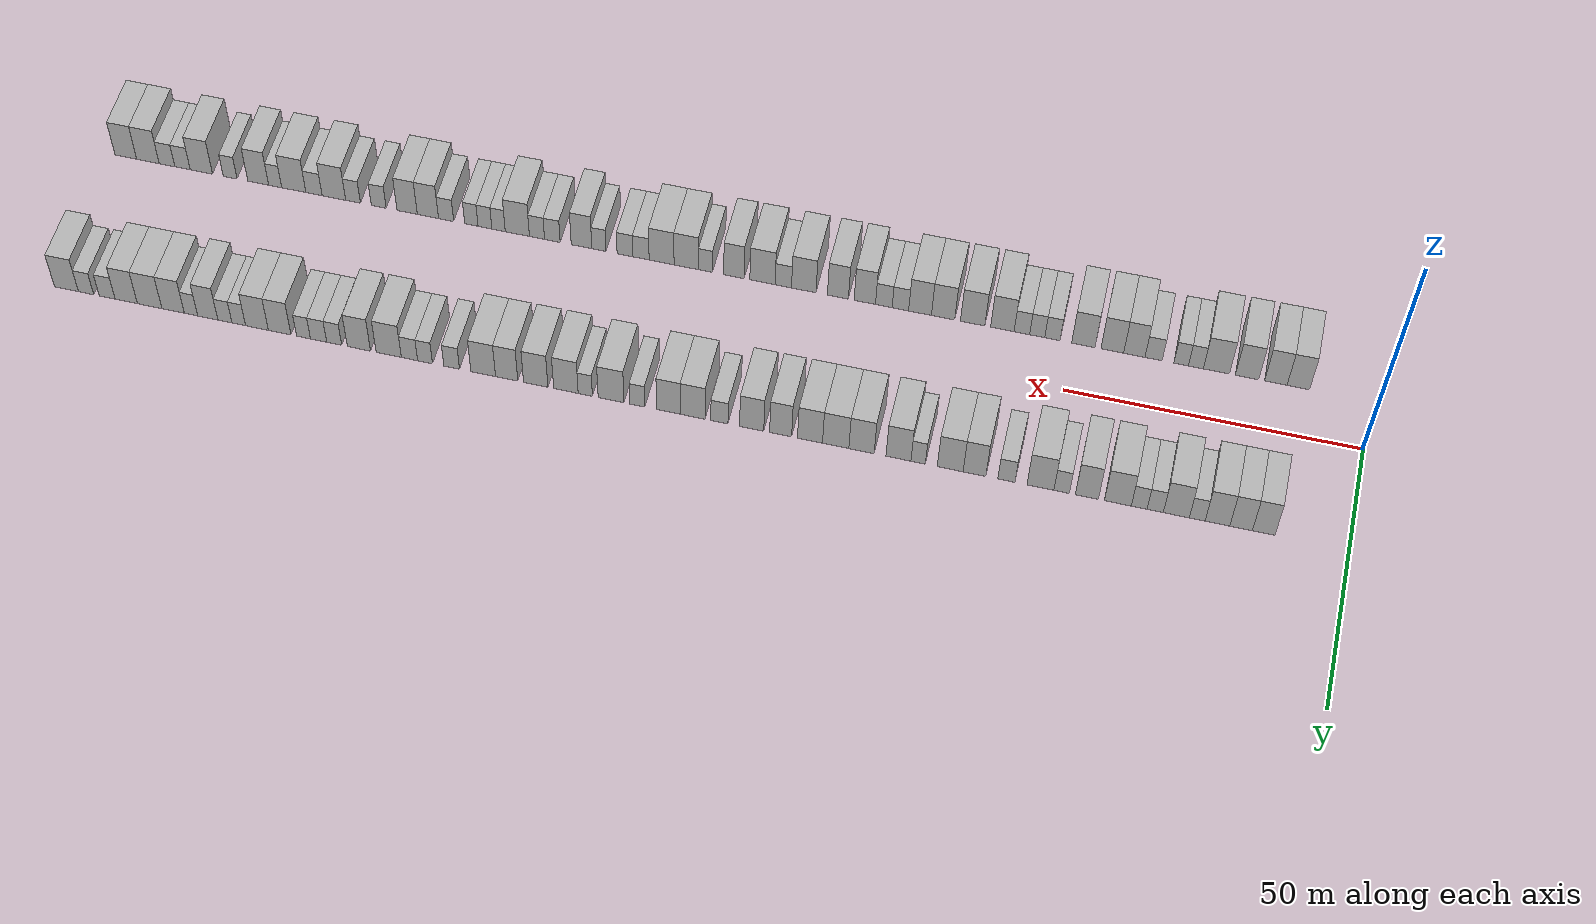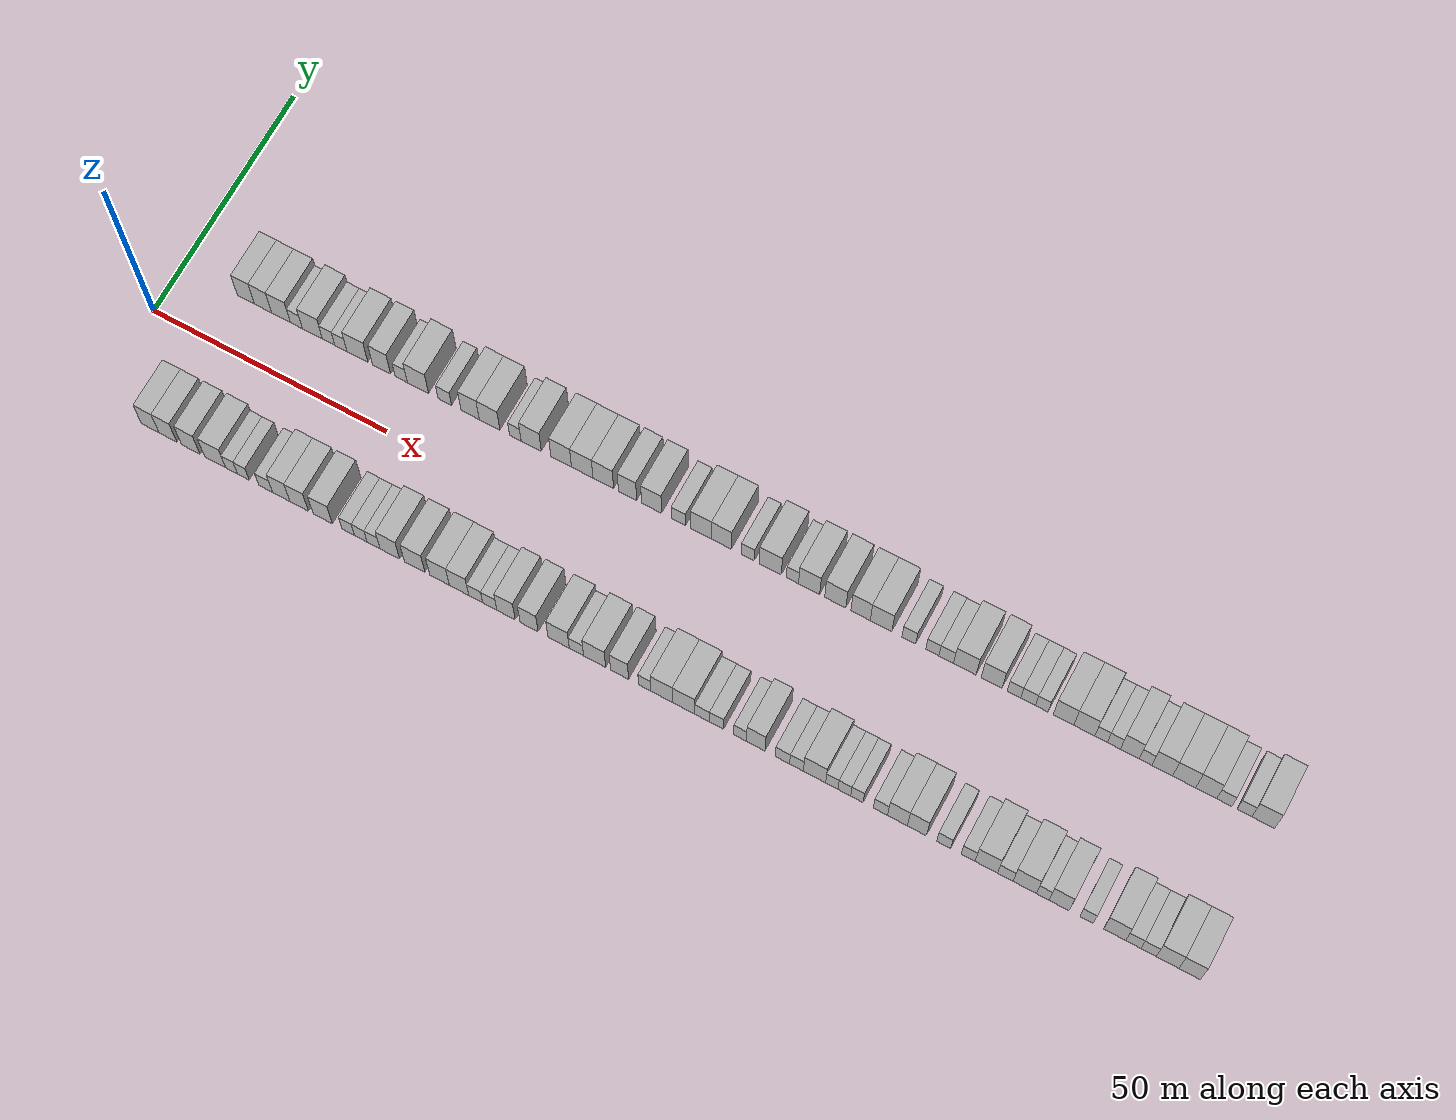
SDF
<sdf version="1.6">
 <world name="default">
  <scene>
   <sky><clouds><speed>12</speed></clouds></sky>
   <ambient>0.4 0.4 0.4 1</ambient>
   <background>0.7 0.7 0.7 1</background>
   <shadows>1</shadows>
  </scene>
  <gravity>0 0 -9.8066</gravity>
  <magnetic_field>6e-06 2.3e-05 -4.2e-05</magnetic_field>
  <physics default="0" name="default_physics" type="ode">
   <ode>
    <solver>
     <type>quick</type>
     <iters>10</iters>
     <sor>1.0</sor>
     <use_dynamic_moi_rescaling>0</use_dynamic_moi_rescaling>
    </solver>
    <constraints>
     <cfm>0</cfm>
     <erp>0.2</erp>
     <contact_max_correcting_vel>100</contact_max_correcting_vel>
     <contact_surface_layer>0.001</contact_surface_layer>
    </constraints>
   </ode>
   <max_step_size>0.004</max_step_size>
   <real_time_factor>1</real_time_factor>
   <real_time_update_rate>250</real_time_update_rate>
  </physics>
  <light name="sun" type="directional">
   <pose>0 0 10 0 0 0</pose>
   <diffuse>0.8 0.8 0.8 1</diffuse>
   <specular>0.2 0.2 0.2 1</specular>
   <attenuation>
    <range>1000</range>
    <constant>0.9</constant>
    <linear>0.01</linear>
    <quadratic>0.001</quadratic>
   </attenuation>
   <direction>-0.5 0.1 -0.9</direction>
  </light>
  <model name="building_1">
   <static>1</static>
   <pose>13.8397 15.0000 0 0.000000 0.000000 1.570796</pose>
   <link name="link">
    <pose>0 0 4.50 0 0 0</pose>
    <collision name="collision"><geometry><box><size>10.0000 3.6794 9.0000</size></box></geometry></collision>
    <visual name="visual">
     <cast_shadows>0</cast_shadows>
     <geometry><box><size>10.0000 3.6794 9.0000</size></box></geometry>
     <material>
      <script>
       <uri>model://HANNAS_wall/materials/scripts</uri>
       <uri>model://HANNAS_wall/materials/textures</uri>
       <name>vrc/HANNAS_wall</name>
      </script>
     </material>
    </visual>
   </link>
  </model>
  <model name="building_2">
   <static>1</static>
   <pose>17.5218 15.0000 0 0.000000 0.000000 1.570796</pose>
   <link name="link">
    <pose>0 0 4.50 0 0 0</pose>
    <collision name="collision"><geometry><box><size>10.0000 3.6849 9.0000</size></box></geometry></collision>
    <visual name="visual">
     <cast_shadows>0</cast_shadows>
     <geometry><box><size>10.0000 3.6849 9.0000</size></box></geometry>
     <material>
      <script>
       <uri>model://HANNAS_wall/materials/scripts</uri>
       <uri>model://HANNAS_wall/materials/textures</uri>
       <name>vrc/HANNAS_wall</name>
      </script>
     </material>
    </visual>
   </link>
  </model>
  <model name="building_3">
   <static>1</static>
   <pose>21.3801 15.0000 0 0.000000 0.000000 1.570796</pose>
   <link name="link">
    <pose>0 0 4.50 0 0 0</pose>
    <collision name="collision"><geometry><box><size>10.0000 4.0316 9.0000</size></box></geometry></collision>
    <visual name="visual">
     <cast_shadows>0</cast_shadows>
     <geometry><box><size>10.0000 4.0316 9.0000</size></box></geometry>
     <material>
      <script>
       <uri>model://HANNAS_wall/materials/scripts</uri>
       <uri>model://HANNAS_wall/materials/textures</uri>
       <name>vrc/HANNAS_wall</name>
      </script>
     </material>
    </visual>
   </link>
  </model>
  <model name="building_4">
   <static>1</static>
   <pose>24.6858 15.0000 0 0.000000 0.000000 1.570796</pose>
   <link name="link">
    <pose>0 0 3.00 0 0 0</pose>
    <collision name="collision"><geometry><box><size>10.0000 2.5798 6.0000</size></box></geometry></collision>
    <visual name="visual">
     <cast_shadows>0</cast_shadows>
     <geometry><box><size>10.0000 2.5798 6.0000</size></box></geometry>
     <material>
      <script>
       <uri>model://HANNAS_wall/materials/scripts</uri>
       <uri>model://HANNAS_wall/materials/textures</uri>
       <name>vrc/HANNAS_wall</name>
      </script>
     </material>
    </visual>
   </link>
  </model>
  <model name="building_5">
   <static>1</static>
   <pose>28.1155 15.0000 0 0.000000 0.000000 1.570796</pose>
   <link name="link">
    <pose>0 0 4.50 0 0 0</pose>
    <collision name="collision"><geometry><box><size>10.0000 4.2796 9.0000</size></box></geometry></collision>
    <visual name="visual">
     <cast_shadows>0</cast_shadows>
     <geometry><box><size>10.0000 4.2796 9.0000</size></box></geometry>
     <material>
      <script>
       <uri>model://HANNAS_wall/materials/scripts</uri>
       <uri>model://HANNAS_wall/materials/textures</uri>
       <name>vrc/HANNAS_wall</name>
      </script>
     </material>
    </visual>
   </link>
  </model>
  <model name="building_6">
   <static>1</static>
   <pose>31.5834 15.0000 0 0.000000 0.000000 1.570796</pose>
   <link name="link">
    <pose>0 0 3.00 0 0 0</pose>
    <collision name="collision"><geometry><box><size>10.0000 2.6562 6.0000</size></box></geometry></collision>
    <visual name="visual">
     <cast_shadows>0</cast_shadows>
     <geometry><box><size>10.0000 2.6562 6.0000</size></box></geometry>
     <material>
      <script>
       <uri>model://HANNAS_wall/materials/scripts</uri>
       <uri>model://HANNAS_wall/materials/textures</uri>
       <name>vrc/HANNAS_wall</name>
      </script>
     </material>
    </visual>
   </link>
  </model>
  <model name="building_7">
   <static>1</static>
   <pose>34.2161 15.0000 0 0.000000 0.000000 1.570796</pose>
   <link name="link">
    <pose>0 0 3.00 0 0 0</pose>
    <collision name="collision"><geometry><box><size>10.0000 2.6093 6.0000</size></box></geometry></collision>
    <visual name="visual">
     <cast_shadows>0</cast_shadows>
     <geometry><box><size>10.0000 2.6093 6.0000</size></box></geometry>
     <material>
      <script>
       <uri>model://HANNAS_wall/materials/scripts</uri>
       <uri>model://HANNAS_wall/materials/textures</uri>
       <name>vrc/HANNAS_wall</name>
      </script>
     </material>
    </visual>
   </link>
  </model>
  <model name="building_8">
   <static>1</static>
   <pose>37.7383 15.0000 0 0.000000 0.000000 1.570796</pose>
   <link name="link">
    <pose>0 0 4.50 0 0 0</pose>
    <collision name="collision"><geometry><box><size>10.0000 4.4352 9.0000</size></box></geometry></collision>
    <visual name="visual">
     <cast_shadows>0</cast_shadows>
     <geometry><box><size>10.0000 4.4352 9.0000</size></box></geometry>
     <material>
      <script>
       <uri>model://HANNAS_wall/materials/scripts</uri>
       <uri>model://HANNAS_wall/materials/textures</uri>
       <name>vrc/HANNAS_wall</name>
      </script>
     </material>
    </visual>
   </link>
  </model>
  <model name="building_9">
   <static>1</static>
   <pose>42.8617 15.0000 0 0.000000 0.000000 1.570796</pose>
   <link name="link">
    <pose>0 0 4.50 0 0 0</pose>
    <collision name="collision"><geometry><box><size>10.0000 3.8115 9.0000</size></box></geometry></collision>
    <visual name="visual">
     <cast_shadows>0</cast_shadows>
     <geometry><box><size>10.0000 3.8115 9.0000</size></box></geometry>
     <material>
      <script>
       <uri>model://HANNAS_wall/materials/scripts</uri>
       <uri>model://HANNAS_wall/materials/textures</uri>
       <name>vrc/HANNAS_wall</name>
      </script>
     </material>
    </visual>
   </link>
  </model>
  <model name="building_10">
   <static>1</static>
   <pose>47.0494 15.0000 0 0.000000 0.000000 1.570796</pose>
   <link name="link">
    <pose>0 0 3.00 0 0 0</pose>
    <collision name="collision"><geometry><box><size>10.0000 2.5639 6.0000</size></box></geometry></collision>
    <visual name="visual">
     <cast_shadows>0</cast_shadows>
     <geometry><box><size>10.0000 2.5639 6.0000</size></box></geometry>
     <material>
      <script>
       <uri>model://HANNAS_wall/materials/scripts</uri>
       <uri>model://HANNAS_wall/materials/textures</uri>
       <name>vrc/HANNAS_wall</name>
      </script>
     </material>
    </visual>
   </link>
  </model>
  <model name="building_11">
   <static>1</static>
   <pose>50.5670 15.0000 0 0.000000 0.000000 1.570796</pose>
   <link name="link">
    <pose>0 0 4.50 0 0 0</pose>
    <collision name="collision"><geometry><box><size>10.0000 4.4715 9.0000</size></box></geometry></collision>
    <visual name="visual">
     <cast_shadows>0</cast_shadows>
     <geometry><box><size>10.0000 4.4715 9.0000</size></box></geometry>
     <material>
      <script>
       <uri>model://HANNAS_wall/materials/scripts</uri>
       <uri>model://HANNAS_wall/materials/textures</uri>
       <name>vrc/HANNAS_wall</name>
      </script>
     </material>
    </visual>
   </link>
  </model>
  <model name="building_12">
   <static>1</static>
   <pose>56.2342 15.0000 0 0.000000 0.000000 1.570796</pose>
   <link name="link">
    <pose>0 0 3.00 0 0 0</pose>
    <collision name="collision"><geometry><box><size>10.0000 2.8628 6.0000</size></box></geometry></collision>
    <visual name="visual">
     <cast_shadows>0</cast_shadows>
     <geometry><box><size>10.0000 2.8628 6.0000</size></box></geometry>
     <material>
      <script>
       <uri>model://HANNAS_wall/materials/scripts</uri>
       <uri>model://HANNAS_wall/materials/textures</uri>
       <name>vrc/HANNAS_wall</name>
      </script>
     </material>
    </visual>
   </link>
  </model>
  <model name="building_13">
   <static>1</static>
   <pose>61.5704 15.0000 0 0.000000 0.000000 1.570796</pose>
   <link name="link">
    <pose>0 0 4.50 0 0 0</pose>
    <collision name="collision"><geometry><box><size>10.0000 3.8097 9.0000</size></box></geometry></collision>
    <visual name="visual">
     <cast_shadows>0</cast_shadows>
     <geometry><box><size>10.0000 3.8097 9.0000</size></box></geometry>
     <material>
      <script>
       <uri>model://HANNAS_wall/materials/scripts</uri>
       <uri>model://HANNAS_wall/materials/textures</uri>
       <name>vrc/HANNAS_wall</name>
      </script>
     </material>
    </visual>
   </link>
  </model>
  <model name="building_14">
   <static>1</static>
   <pose>65.6387 15.0000 0 0.000000 0.000000 1.570796</pose>
   <link name="link">
    <pose>0 0 4.50 0 0 0</pose>
    <collision name="collision"><geometry><box><size>10.0000 4.3270 9.0000</size></box></geometry></collision>
    <visual name="visual">
     <cast_shadows>0</cast_shadows>
     <geometry><box><size>10.0000 4.3270 9.0000</size></box></geometry>
     <material>
      <script>
       <uri>model://HANNAS_wall/materials/scripts</uri>
       <uri>model://HANNAS_wall/materials/textures</uri>
       <name>vrc/HANNAS_wall</name>
      </script>
     </material>
    </visual>
   </link>
  </model>
  <model name="building_15">
   <static>1</static>
   <pose>71.0189 15.0000 0 0.000000 0.000000 1.570796</pose>
   <link name="link">
    <pose>0 0 3.00 0 0 0</pose>
    <collision name="collision"><geometry><box><size>10.0000 2.4332 6.0000</size></box></geometry></collision>
    <visual name="visual">
     <cast_shadows>0</cast_shadows>
     <geometry><box><size>10.0000 2.4332 6.0000</size></box></geometry>
     <material>
      <script>
       <uri>model://HANNAS_wall/materials/scripts</uri>
       <uri>model://HANNAS_wall/materials/textures</uri>
       <name>vrc/HANNAS_wall</name>
      </script>
     </material>
    </visual>
   </link>
  </model>
  <model name="building_16">
   <static>1</static>
   <pose>74.3353 15.0000 0 0.000000 0.000000 1.570796</pose>
   <link name="link">
    <pose>0 0 4.50 0 0 0</pose>
    <collision name="collision"><geometry><box><size>10.0000 4.1997 9.0000</size></box></geometry></collision>
    <visual name="visual">
     <cast_shadows>0</cast_shadows>
     <geometry><box><size>10.0000 4.1997 9.0000</size></box></geometry>
     <material>
      <script>
       <uri>model://HANNAS_wall/materials/scripts</uri>
       <uri>model://HANNAS_wall/materials/textures</uri>
       <name>vrc/HANNAS_wall</name>
      </script>
     </material>
    </visual>
   </link>
  </model>
  <model name="building_17">
   <static>1</static>
   <pose>80.5745 15.0000 0 0.000000 0.000000 1.570796</pose>
   <link name="link">
    <pose>0 0 4.50 0 0 0</pose>
    <collision name="collision"><geometry><box><size>10.0000 4.2787 9.0000</size></box></geometry></collision>
    <visual name="visual">
     <cast_shadows>0</cast_shadows>
     <geometry><box><size>10.0000 4.2787 9.0000</size></box></geometry>
     <material>
      <script>
       <uri>model://HANNAS_wall/materials/scripts</uri>
       <uri>model://HANNAS_wall/materials/textures</uri>
       <name>vrc/HANNAS_wall</name>
      </script>
     </material>
    </visual>
   </link>
  </model>
  <model name="building_18">
   <static>1</static>
   <pose>84.9429 15.0000 0 0.000000 0.000000 1.570796</pose>
   <link name="link">
    <pose>0 0 4.50 0 0 0</pose>
    <collision name="collision"><geometry><box><size>10.0000 4.4583 9.0000</size></box></geometry></collision>
    <visual name="visual">
     <cast_shadows>0</cast_shadows>
     <geometry><box><size>10.0000 4.4583 9.0000</size></box></geometry>
     <material>
      <script>
       <uri>model://HANNAS_wall/materials/scripts</uri>
       <uri>model://HANNAS_wall/materials/textures</uri>
       <name>vrc/HANNAS_wall</name>
      </script>
     </material>
    </visual>
   </link>
  </model>
  <model name="building_19">
   <static>1</static>
   <pose>89.2964 15.0000 0 0.000000 0.000000 1.570796</pose>
   <link name="link">
    <pose>0 0 4.50 0 0 0</pose>
    <collision name="collision"><geometry><box><size>10.0000 4.2488 9.0000</size></box></geometry></collision>
    <visual name="visual">
     <cast_shadows>0</cast_shadows>
     <geometry><box><size>10.0000 4.2488 9.0000</size></box></geometry>
     <material>
      <script>
       <uri>model://HANNAS_wall/materials/scripts</uri>
       <uri>model://HANNAS_wall/materials/textures</uri>
       <name>vrc/HANNAS_wall</name>
      </script>
     </material>
    </visual>
   </link>
  </model>
  <model name="building_20">
   <static>1</static>
   <pose>94.2962 15.0000 0 0.000000 0.000000 1.570796</pose>
   <link name="link">
    <pose>0 0 4.50 0 0 0</pose>
    <collision name="collision"><geometry><box><size>10.0000 3.7507 9.0000</size></box></geometry></collision>
    <visual name="visual">
     <cast_shadows>0</cast_shadows>
     <geometry><box><size>10.0000 3.7507 9.0000</size></box></geometry>
     <material>
      <script>
       <uri>model://HANNAS_wall/materials/scripts</uri>
       <uri>model://HANNAS_wall/materials/textures</uri>
       <name>vrc/HANNAS_wall</name>
      </script>
     </material>
    </visual>
   </link>
  </model>
  <model name="building_21">
   <static>1</static>
   <pose>99.2326 15.0000 0 0.000000 0.000000 1.570796</pose>
   <link name="link">
    <pose>0 0 4.50 0 0 0</pose>
    <collision name="collision"><geometry><box><size>10.0000 4.1222 9.0000</size></box></geometry></collision>
    <visual name="visual">
     <cast_shadows>0</cast_shadows>
     <geometry><box><size>10.0000 4.1222 9.0000</size></box></geometry>
     <material>
      <script>
       <uri>model://HANNAS_wall/materials/scripts</uri>
       <uri>model://HANNAS_wall/materials/textures</uri>
       <name>vrc/HANNAS_wall</name>
      </script>
     </material>
    </visual>
   </link>
  </model>
  <model name="building_22">
   <static>1</static>
   <pose>104.7581 15.0000 0 0.000000 0.000000 1.570796</pose>
   <link name="link">
    <pose>0 0 3.00 0 0 0</pose>
    <collision name="collision"><geometry><box><size>10.0000 2.9286 6.0000</size></box></geometry></collision>
    <visual name="visual">
     <cast_shadows>0</cast_shadows>
     <geometry><box><size>10.0000 2.9286 6.0000</size></box></geometry>
     <material>
      <script>
       <uri>model://HANNAS_wall/materials/scripts</uri>
       <uri>model://HANNAS_wall/materials/textures</uri>
       <name>vrc/HANNAS_wall</name>
      </script>
     </material>
    </visual>
   </link>
  </model>
  <model name="building_23">
   <static>1</static>
   <pose>109.3536 15.0000 0 0.000000 0.000000 1.570796</pose>
   <link name="link">
    <pose>0 0 4.50 0 0 0</pose>
    <collision name="collision"><geometry><box><size>10.0000 4.2624 9.0000</size></box></geometry></collision>
    <visual name="visual">
     <cast_shadows>0</cast_shadows>
     <geometry><box><size>10.0000 4.2624 9.0000</size></box></geometry>
     <material>
      <script>
       <uri>model://HANNAS_wall/materials/scripts</uri>
       <uri>model://HANNAS_wall/materials/textures</uri>
       <name>vrc/HANNAS_wall</name>
      </script>
     </material>
    </visual>
   </link>
  </model>
  <model name="building_24">
   <static>1</static>
   <pose>113.5259 15.0000 0 0.000000 0.000000 1.570796</pose>
   <link name="link">
    <pose>0 0 4.50 0 0 0</pose>
    <collision name="collision"><geometry><box><size>10.0000 4.0823 9.0000</size></box></geometry></collision>
    <visual name="visual">
     <cast_shadows>0</cast_shadows>
     <geometry><box><size>10.0000 4.0823 9.0000</size></box></geometry>
     <material>
      <script>
       <uri>model://HANNAS_wall/materials/scripts</uri>
       <uri>model://HANNAS_wall/materials/textures</uri>
       <name>vrc/HANNAS_wall</name>
      </script>
     </material>
    </visual>
   </link>
  </model>
  <model name="building_25">
   <static>1</static>
   <pose>118.8828 15.0000 0 0.000000 0.000000 1.570796</pose>
   <link name="link">
    <pose>0 0 3.00 0 0 0</pose>
    <collision name="collision"><geometry><box><size>10.0000 2.6316 6.0000</size></box></geometry></collision>
    <visual name="visual">
     <cast_shadows>0</cast_shadows>
     <geometry><box><size>10.0000 2.6316 6.0000</size></box></geometry>
     <material>
      <script>
       <uri>model://HANNAS_wall/materials/scripts</uri>
       <uri>model://HANNAS_wall/materials/textures</uri>
       <name>vrc/HANNAS_wall</name>
      </script>
     </material>
    </visual>
   </link>
  </model>
  <model name="building_26">
   <static>1</static>
   <pose>123.4322 15.0000 0 0.000000 0.000000 1.570796</pose>
   <link name="link">
    <pose>0 0 4.50 0 0 0</pose>
    <collision name="collision"><geometry><box><size>10.0000 4.4671 9.0000</size></box></geometry></collision>
    <visual name="visual">
     <cast_shadows>0</cast_shadows>
     <geometry><box><size>10.0000 4.4671 9.0000</size></box></geometry>
     <material>
      <script>
       <uri>model://HANNAS_wall/materials/scripts</uri>
       <uri>model://HANNAS_wall/materials/textures</uri>
       <name>vrc/HANNAS_wall</name>
      </script>
     </material>
    </visual>
   </link>
  </model>
  <model name="building_27">
   <static>1</static>
   <pose>127.9022 15.0000 0 0.000000 0.000000 1.570796</pose>
   <link name="link">
    <pose>0 0 3.00 0 0 0</pose>
    <collision name="collision"><geometry><box><size>10.0000 2.4729 6.0000</size></box></geometry></collision>
    <visual name="visual">
     <cast_shadows>0</cast_shadows>
     <geometry><box><size>10.0000 2.4729 6.0000</size></box></geometry>
     <material>
      <script>
       <uri>model://HANNAS_wall/materials/scripts</uri>
       <uri>model://HANNAS_wall/materials/textures</uri>
       <name>vrc/HANNAS_wall</name>
      </script>
     </material>
    </visual>
   </link>
  </model>
  <model name="building_28">
   <static>1</static>
   <pose>131.2680 15.0000 0 0.000000 0.000000 1.570796</pose>
   <link name="link">
    <pose>0 0 4.50 0 0 0</pose>
    <collision name="collision"><geometry><box><size>10.0000 4.2587 9.0000</size></box></geometry></collision>
    <visual name="visual">
     <cast_shadows>0</cast_shadows>
     <geometry><box><size>10.0000 4.2587 9.0000</size></box></geometry>
     <material>
      <script>
       <uri>model://HANNAS_wall/materials/scripts</uri>
       <uri>model://HANNAS_wall/materials/textures</uri>
       <name>vrc/HANNAS_wall</name>
      </script>
     </material>
    </visual>
   </link>
  </model>
  <model name="building_29">
   <static>1</static>
   <pose>136.5224 15.0000 0 0.000000 0.000000 1.570796</pose>
   <link name="link">
    <pose>0 0 4.50 0 0 0</pose>
    <collision name="collision"><geometry><box><size>10.0000 4.2500 9.0000</size></box></geometry></collision>
    <visual name="visual">
     <cast_shadows>0</cast_shadows>
     <geometry><box><size>10.0000 4.2500 9.0000</size></box></geometry>
     <material>
      <script>
       <uri>model://HANNAS_wall/materials/scripts</uri>
       <uri>model://HANNAS_wall/materials/textures</uri>
       <name>vrc/HANNAS_wall</name>
      </script>
     </material>
    </visual>
   </link>
  </model>
  <model name="building_30">
   <static>1</static>
   <pose>141.5976 15.0000 0 0.000000 0.000000 1.570796</pose>
   <link name="link">
    <pose>0 0 4.50 0 0 0</pose>
    <collision name="collision"><geometry><box><size>10.0000 3.9003 9.0000</size></box></geometry></collision>
    <visual name="visual">
     <cast_shadows>0</cast_shadows>
     <geometry><box><size>10.0000 3.9003 9.0000</size></box></geometry>
     <material>
      <script>
       <uri>model://HANNAS_wall/materials/scripts</uri>
       <uri>model://HANNAS_wall/materials/textures</uri>
       <name>vrc/HANNAS_wall</name>
      </script>
     </material>
    </visual>
   </link>
  </model>
  <model name="building_31">
   <static>1</static>
   <pose>145.7080 15.0000 0 0.000000 0.000000 1.570796</pose>
   <link name="link">
    <pose>0 0 4.50 0 0 0</pose>
    <collision name="collision"><geometry><box><size>10.0000 4.3205 9.0000</size></box></geometry></collision>
    <visual name="visual">
     <cast_shadows>0</cast_shadows>
     <geometry><box><size>10.0000 4.3205 9.0000</size></box></geometry>
     <material>
      <script>
       <uri>model://HANNAS_wall/materials/scripts</uri>
       <uri>model://HANNAS_wall/materials/textures</uri>
       <name>vrc/HANNAS_wall</name>
      </script>
     </material>
    </visual>
   </link>
  </model>
  <model name="building_32">
   <static>1</static>
   <pose>151.2421 15.0000 0 0.000000 0.000000 1.570796</pose>
   <link name="link">
    <pose>0 0 3.00 0 0 0</pose>
    <collision name="collision"><geometry><box><size>10.0000 2.7479 6.0000</size></box></geometry></collision>
    <visual name="visual">
     <cast_shadows>0</cast_shadows>
     <geometry><box><size>10.0000 2.7479 6.0000</size></box></geometry>
     <material>
      <script>
       <uri>model://HANNAS_wall/materials/scripts</uri>
       <uri>model://HANNAS_wall/materials/textures</uri>
       <name>vrc/HANNAS_wall</name>
      </script>
     </material>
    </visual>
   </link>
  </model>
  <model name="building_33">
   <static>1</static>
   <pose>155.9254 15.0000 0 0.000000 0.000000 1.570796</pose>
   <link name="link">
    <pose>0 0 3.00 0 0 0</pose>
    <collision name="collision"><geometry><box><size>10.0000 2.6187 6.0000</size></box></geometry></collision>
    <visual name="visual">
     <cast_shadows>0</cast_shadows>
     <geometry><box><size>10.0000 2.6187 6.0000</size></box></geometry>
     <material>
      <script>
       <uri>model://HANNAS_wall/materials/scripts</uri>
       <uri>model://HANNAS_wall/materials/textures</uri>
       <name>vrc/HANNAS_wall</name>
      </script>
     </material>
    </visual>
   </link>
  </model>
  <model name="building_34">
   <static>1</static>
   <pose>158.6791 15.0000 0 0.000000 0.000000 1.570796</pose>
   <link name="link">
    <pose>0 0 3.00 0 0 0</pose>
    <collision name="collision"><geometry><box><size>10.0000 2.8888 6.0000</size></box></geometry></collision>
    <visual name="visual">
     <cast_shadows>0</cast_shadows>
     <geometry><box><size>10.0000 2.8888 6.0000</size></box></geometry>
     <material>
      <script>
       <uri>model://HANNAS_wall/materials/scripts</uri>
       <uri>model://HANNAS_wall/materials/textures</uri>
       <name>vrc/HANNAS_wall</name>
      </script>
     </material>
    </visual>
   </link>
  </model>
  <model name="building_35">
   <static>1</static>
   <pose>162.3498 15.0000 0 0.000000 0.000000 1.570796</pose>
   <link name="link">
    <pose>0 0 4.50 0 0 0</pose>
    <collision name="collision"><geometry><box><size>10.0000 4.4525 9.0000</size></box></geometry></collision>
    <visual name="visual">
     <cast_shadows>0</cast_shadows>
     <geometry><box><size>10.0000 4.4525 9.0000</size></box></geometry>
     <material>
      <script>
       <uri>model://HANNAS_wall/materials/scripts</uri>
       <uri>model://HANNAS_wall/materials/textures</uri>
       <name>vrc/HANNAS_wall</name>
      </script>
     </material>
    </visual>
   </link>
  </model>
  <model name="building_36">
   <static>1</static>
   <pose>167.6373 15.0000 0 0.000000 0.000000 1.570796</pose>
   <link name="link">
    <pose>0 0 4.50 0 0 0</pose>
    <collision name="collision"><geometry><box><size>10.0000 4.1225 9.0000</size></box></geometry></collision>
    <visual name="visual">
     <cast_shadows>0</cast_shadows>
     <geometry><box><size>10.0000 4.1225 9.0000</size></box></geometry>
     <material>
      <script>
       <uri>model://HANNAS_wall/materials/scripts</uri>
       <uri>model://HANNAS_wall/materials/textures</uri>
       <name>vrc/HANNAS_wall</name>
      </script>
     </material>
    </visual>
   </link>
  </model>
  <model name="building_37">
   <static>1</static>
   <pose>172.0362 15.0000 0 0.000000 0.000000 1.570796</pose>
   <link name="link">
    <pose>0 0 3.00 0 0 0</pose>
    <collision name="collision"><geometry><box><size>10.0000 2.6752 6.0000</size></box></geometry></collision>
    <visual name="visual">
     <cast_shadows>0</cast_shadows>
     <geometry><box><size>10.0000 2.6752 6.0000</size></box></geometry>
     <material>
      <script>
       <uri>model://HANNAS_wall/materials/scripts</uri>
       <uri>model://HANNAS_wall/materials/textures</uri>
       <name>vrc/HANNAS_wall</name>
      </script>
     </material>
    </visual>
   </link>
  </model>
  <model name="building_38">
   <static>1</static>
   <pose>174.8219 15.0000 0 0.000000 0.000000 1.570796</pose>
   <link name="link">
    <pose>0 0 3.00 0 0 0</pose>
    <collision name="collision"><geometry><box><size>10.0000 2.8962 6.0000</size></box></geometry></collision>
    <visual name="visual">
     <cast_shadows>0</cast_shadows>
     <geometry><box><size>10.0000 2.8962 6.0000</size></box></geometry>
     <material>
      <script>
       <uri>model://HANNAS_wall/materials/scripts</uri>
       <uri>model://HANNAS_wall/materials/textures</uri>
       <name>vrc/HANNAS_wall</name>
      </script>
     </material>
    </visual>
   </link>
  </model>
  <model name="building_39">
   <static>1</static>
   <pose>177.5052 15.0000 0 0.000000 0.000000 1.570796</pose>
   <link name="link">
    <pose>0 0 3.00 0 0 0</pose>
    <collision name="collision"><geometry><box><size>10.0000 2.4705 6.0000</size></box></geometry></collision>
    <visual name="visual">
     <cast_shadows>0</cast_shadows>
     <geometry><box><size>10.0000 2.4705 6.0000</size></box></geometry>
     <material>
      <script>
       <uri>model://HANNAS_wall/materials/scripts</uri>
       <uri>model://HANNAS_wall/materials/textures</uri>
       <name>vrc/HANNAS_wall</name>
      </script>
     </material>
    </visual>
   </link>
  </model>
  <model name="building_40">
   <static>1</static>
   <pose>181.7657 15.0000 0 0.000000 0.000000 1.570796</pose>
   <link name="link">
    <pose>0 0 4.50 0 0 0</pose>
    <collision name="collision"><geometry><box><size>10.0000 4.0505 9.0000</size></box></geometry></collision>
    <visual name="visual">
     <cast_shadows>0</cast_shadows>
     <geometry><box><size>10.0000 4.0505 9.0000</size></box></geometry>
     <material>
      <script>
       <uri>model://HANNAS_wall/materials/scripts</uri>
       <uri>model://HANNAS_wall/materials/textures</uri>
       <name>vrc/HANNAS_wall</name>
      </script>
     </material>
    </visual>
   </link>
  </model>
  <model name="building_41">
   <static>1</static>
   <pose>185.8350 15.0000 0 0.000000 0.000000 1.570796</pose>
   <link name="link">
    <pose>0 0 4.50 0 0 0</pose>
    <collision name="collision"><geometry><box><size>10.0000 4.0880 9.0000</size></box></geometry></collision>
    <visual name="visual">
     <cast_shadows>0</cast_shadows>
     <geometry><box><size>10.0000 4.0880 9.0000</size></box></geometry>
     <material>
      <script>
       <uri>model://HANNAS_wall/materials/scripts</uri>
       <uri>model://HANNAS_wall/materials/textures</uri>
       <name>vrc/HANNAS_wall</name>
      </script>
     </material>
    </visual>
   </link>
  </model>
  <model name="building_42">
   <static>1</static>
   <pose>189.0985 15.0000 0 0.000000 0.000000 1.570796</pose>
   <link name="link">
    <pose>0 0 3.00 0 0 0</pose>
    <collision name="collision"><geometry><box><size>10.0000 2.4391 6.0000</size></box></geometry></collision>
    <visual name="visual">
     <cast_shadows>0</cast_shadows>
     <geometry><box><size>10.0000 2.4391 6.0000</size></box></geometry>
     <material>
      <script>
       <uri>model://HANNAS_wall/materials/scripts</uri>
       <uri>model://HANNAS_wall/materials/textures</uri>
       <name>vrc/HANNAS_wall</name>
      </script>
     </material>
    </visual>
   </link>
  </model>
  <model name="building_43">
   <static>1</static>
   <pose>191.5861 15.0000 0 0.000000 0.000000 1.570796</pose>
   <link name="link">
    <pose>0 0 3.00 0 0 0</pose>
    <collision name="collision"><geometry><box><size>10.0000 2.5361 6.0000</size></box></geometry></collision>
    <visual name="visual">
     <cast_shadows>0</cast_shadows>
     <geometry><box><size>10.0000 2.5361 6.0000</size></box></geometry>
     <material>
      <script>
       <uri>model://HANNAS_wall/materials/scripts</uri>
       <uri>model://HANNAS_wall/materials/textures</uri>
       <name>vrc/HANNAS_wall</name>
      </script>
     </material>
    </visual>
   </link>
  </model>
  <model name="building_44">
   <static>1</static>
   <pose>194.6744 15.0000 0 0.000000 0.000000 1.570796</pose>
   <link name="link">
    <pose>0 0 4.50 0 0 0</pose>
    <collision name="collision"><geometry><box><size>10.0000 3.6403 9.0000</size></box></geometry></collision>
    <visual name="visual">
     <cast_shadows>0</cast_shadows>
     <geometry><box><size>10.0000 3.6403 9.0000</size></box></geometry>
     <material>
      <script>
       <uri>model://HANNAS_wall/materials/scripts</uri>
       <uri>model://HANNAS_wall/materials/textures</uri>
       <name>vrc/HANNAS_wall</name>
      </script>
     </material>
    </visual>
   </link>
  </model>
  <model name="building_45">
   <static>1</static>
   <pose>197.7072 15.0000 0 0.000000 0.000000 1.570796</pose>
   <link name="link">
    <pose>0 0 3.00 0 0 0</pose>
    <collision name="collision"><geometry><box><size>10.0000 2.4253 6.0000</size></box></geometry></collision>
    <visual name="visual">
     <cast_shadows>0</cast_shadows>
     <geometry><box><size>10.0000 2.4253 6.0000</size></box></geometry>
     <material>
      <script>
       <uri>model://HANNAS_wall/materials/scripts</uri>
       <uri>model://HANNAS_wall/materials/textures</uri>
       <name>vrc/HANNAS_wall</name>
      </script>
     </material>
    </visual>
   </link>
  </model>
  <model name="building_46">
   <static>1</static>
   <pose>200.9372 15.0000 0 0.000000 0.000000 1.570796</pose>
   <link name="link">
    <pose>0 0 4.50 0 0 0</pose>
    <collision name="collision"><geometry><box><size>10.0000 4.0347 9.0000</size></box></geometry></collision>
    <visual name="visual">
     <cast_shadows>0</cast_shadows>
     <geometry><box><size>10.0000 4.0347 9.0000</size></box></geometry>
     <material>
      <script>
       <uri>model://HANNAS_wall/materials/scripts</uri>
       <uri>model://HANNAS_wall/materials/textures</uri>
       <name>vrc/HANNAS_wall</name>
      </script>
     </material>
    </visual>
   </link>
  </model>
  <model name="building_47">
   <static>1</static>
   <pose>205.1812 15.0000 0 0.000000 0.000000 1.570796</pose>
   <link name="link">
    <pose>0 0 4.50 0 0 0</pose>
    <collision name="collision"><geometry><box><size>10.0000 4.4534 9.0000</size></box></geometry></collision>
    <visual name="visual">
     <cast_shadows>0</cast_shadows>
     <geometry><box><size>10.0000 4.4534 9.0000</size></box></geometry>
     <material>
      <script>
       <uri>model://HANNAS_wall/materials/scripts</uri>
       <uri>model://HANNAS_wall/materials/textures</uri>
       <name>vrc/HANNAS_wall</name>
      </script>
     </material>
    </visual>
   </link>
  </model>
  <model name="building_48">
   <static>1</static>
   <pose>209.4274 15.0000 0 0.000000 0.000000 1.570796</pose>
   <link name="link">
    <pose>0 0 4.50 0 0 0</pose>
    <collision name="collision"><geometry><box><size>10.0000 4.0390 9.0000</size></box></geometry></collision>
    <visual name="visual">
     <cast_shadows>0</cast_shadows>
     <geometry><box><size>10.0000 4.0390 9.0000</size></box></geometry>
     <material>
      <script>
       <uri>model://HANNAS_wall/materials/scripts</uri>
       <uri>model://HANNAS_wall/materials/textures</uri>
       <name>vrc/HANNAS_wall</name>
      </script>
     </material>
    </visual>
   </link>
  </model>
  <model name="building_49">
   <static>1</static>
   <pose>212.8988 15.0000 0 0.000000 0.000000 1.570796</pose>
   <link name="link">
    <pose>0 0 3.00 0 0 0</pose>
    <collision name="collision"><geometry><box><size>10.0000 2.9038 6.0000</size></box></geometry></collision>
    <visual name="visual">
     <cast_shadows>0</cast_shadows>
     <geometry><box><size>10.0000 2.9038 6.0000</size></box></geometry>
     <material>
      <script>
       <uri>model://HANNAS_wall/materials/scripts</uri>
       <uri>model://HANNAS_wall/materials/textures</uri>
       <name>vrc/HANNAS_wall</name>
      </script>
     </material>
    </visual>
   </link>
  </model>
  <model name="building_50">
   <static>1</static>
   <pose>216.7484 15.0000 0 0.000000 0.000000 1.570796</pose>
   <link name="link">
    <pose>0 0 3.00 0 0 0</pose>
    <collision name="collision"><geometry><box><size>10.0000 2.7955 6.0000</size></box></geometry></collision>
    <visual name="visual">
     <cast_shadows>0</cast_shadows>
     <geometry><box><size>10.0000 2.7955 6.0000</size></box></geometry>
     <material>
      <script>
       <uri>model://HANNAS_wall/materials/scripts</uri>
       <uri>model://HANNAS_wall/materials/textures</uri>
       <name>vrc/HANNAS_wall</name>
      </script>
     </material>
    </visual>
   </link>
  </model>
  <model name="building_51">
   <static>1</static>
   <pose>220.3315 15.0000 0 0.000000 0.000000 1.570796</pose>
   <link name="link">
    <pose>0 0 4.50 0 0 0</pose>
    <collision name="collision"><geometry><box><size>10.0000 4.3706 9.0000</size></box></geometry></collision>
    <visual name="visual">
     <cast_shadows>0</cast_shadows>
     <geometry><box><size>10.0000 4.3706 9.0000</size></box></geometry>
     <material>
      <script>
       <uri>model://HANNAS_wall/materials/scripts</uri>
       <uri>model://HANNAS_wall/materials/textures</uri>
       <name>vrc/HANNAS_wall</name>
      </script>
     </material>
    </visual>
   </link>
  </model>
  <model name="building_52">
   <static>1</static>
   <pose>11.8952 -15.0000 0 0.000000 0.000000 1.570796</pose>
   <link name="link">
    <pose>0 0 4.50 0 0 0</pose>
    <collision name="collision"><geometry><box><size>10.0000 3.7903 9.0000</size></box></geometry></collision>
    <visual name="visual">
     <cast_shadows>0</cast_shadows>
     <geometry><box><size>10.0000 3.7903 9.0000</size></box></geometry>
     <material>
      <script>
       <uri>model://HANNAS_wall/materials/scripts</uri>
       <uri>model://HANNAS_wall/materials/textures</uri>
       <name>vrc/HANNAS_wall</name>
      </script>
     </material>
    </visual>
   </link>
  </model>
  <model name="building_53">
   <static>1</static>
   <pose>15.6842 -15.0000 0 0.000000 0.000000 1.570796</pose>
   <link name="link">
    <pose>0 0 4.50 0 0 0</pose>
    <collision name="collision"><geometry><box><size>10.0000 3.7877 9.0000</size></box></geometry></collision>
    <visual name="visual">
     <cast_shadows>0</cast_shadows>
     <geometry><box><size>10.0000 3.7877 9.0000</size></box></geometry>
     <material>
      <script>
       <uri>model://HANNAS_wall/materials/scripts</uri>
       <uri>model://HANNAS_wall/materials/textures</uri>
       <name>vrc/HANNAS_wall</name>
      </script>
     </material>
    </visual>
   </link>
  </model>
  <model name="building_54">
   <static>1</static>
   <pose>20.5455 -15.0000 0 0.000000 0.000000 1.570796</pose>
   <link name="link">
    <pose>0 0 4.50 0 0 0</pose>
    <collision name="collision"><geometry><box><size>10.0000 3.9350 9.0000</size></box></geometry></collision>
    <visual name="visual">
     <cast_shadows>0</cast_shadows>
     <geometry><box><size>10.0000 3.9350 9.0000</size></box></geometry>
     <material>
      <script>
       <uri>model://HANNAS_wall/materials/scripts</uri>
       <uri>model://HANNAS_wall/materials/textures</uri>
       <name>vrc/HANNAS_wall</name>
      </script>
     </material>
    </visual>
   </link>
  </model>
  <model name="building_55">
   <static>1</static>
   <pose>25.7320 -15.0000 0 0.000000 0.000000 1.570796</pose>
   <link name="link">
    <pose>0 0 4.50 0 0 0</pose>
    <collision name="collision"><geometry><box><size>10.0000 4.4380 9.0000</size></box></geometry></collision>
    <visual name="visual">
     <cast_shadows>0</cast_shadows>
     <geometry><box><size>10.0000 4.4380 9.0000</size></box></geometry>
     <material>
      <script>
       <uri>model://HANNAS_wall/materials/scripts</uri>
       <uri>model://HANNAS_wall/materials/textures</uri>
       <name>vrc/HANNAS_wall</name>
      </script>
     </material>
    </visual>
   </link>
  </model>
  <model name="building_56">
   <static>1</static>
   <pose>29.2053 -15.0000 0 0.000000 0.000000 1.570796</pose>
   <link name="link">
    <pose>0 0 3.00 0 0 0</pose>
    <collision name="collision"><geometry><box><size>10.0000 2.5085 6.0000</size></box></geometry></collision>
    <visual name="visual">
     <cast_shadows>0</cast_shadows>
     <geometry><box><size>10.0000 2.5085 6.0000</size></box></geometry>
     <material>
      <script>
       <uri>model://HANNAS_wall/materials/scripts</uri>
       <uri>model://HANNAS_wall/materials/textures</uri>
       <name>vrc/HANNAS_wall</name>
      </script>
     </material>
    </visual>
   </link>
  </model>
  <model name="building_57">
   <static>1</static>
   <pose>31.7024 -15.0000 0 0.000000 0.000000 1.570796</pose>
   <link name="link">
    <pose>0 0 3.00 0 0 0</pose>
    <collision name="collision"><geometry><box><size>10.0000 2.4858 6.0000</size></box></geometry></collision>
    <visual name="visual">
     <cast_shadows>0</cast_shadows>
     <geometry><box><size>10.0000 2.4858 6.0000</size></box></geometry>
     <material>
      <script>
       <uri>model://HANNAS_wall/materials/scripts</uri>
       <uri>model://HANNAS_wall/materials/textures</uri>
       <name>vrc/HANNAS_wall</name>
      </script>
     </material>
    </visual>
   </link>
  </model>
  <model name="building_58">
   <static>1</static>
   <pose>36.4088 -15.0000 0 0.000000 0.000000 1.570796</pose>
   <link name="link">
    <pose>0 0 3.00 0 0 0</pose>
    <collision name="collision"><geometry><box><size>10.0000 2.9269 6.0000</size></box></geometry></collision>
    <visual name="visual">
     <cast_shadows>0</cast_shadows>
     <geometry><box><size>10.0000 2.9269 6.0000</size></box></geometry>
     <material>
      <script>
       <uri>model://HANNAS_wall/materials/scripts</uri>
       <uri>model://HANNAS_wall/materials/textures</uri>
       <name>vrc/HANNAS_wall</name>
      </script>
     </material>
    </visual>
   </link>
  </model>
  <model name="building_59">
   <static>1</static>
   <pose>39.6919 -15.0000 0 0.000000 0.000000 1.570796</pose>
   <link name="link">
    <pose>0 0 4.50 0 0 0</pose>
    <collision name="collision"><geometry><box><size>10.0000 3.6393 9.0000</size></box></geometry></collision>
    <visual name="visual">
     <cast_shadows>0</cast_shadows>
     <geometry><box><size>10.0000 3.6393 9.0000</size></box></geometry>
     <material>
      <script>
       <uri>model://HANNAS_wall/materials/scripts</uri>
       <uri>model://HANNAS_wall/materials/textures</uri>
       <name>vrc/HANNAS_wall</name>
      </script>
     </material>
    </visual>
   </link>
  </model>
  <model name="building_60">
   <static>1</static>
   <pose>43.4599 -15.0000 0 0.000000 0.000000 1.570796</pose>
   <link name="link">
    <pose>0 0 4.50 0 0 0</pose>
    <collision name="collision"><geometry><box><size>10.0000 3.8965 9.0000</size></box></geometry></collision>
    <visual name="visual">
     <cast_shadows>0</cast_shadows>
     <geometry><box><size>10.0000 3.8965 9.0000</size></box></geometry>
     <material>
      <script>
       <uri>model://HANNAS_wall/materials/scripts</uri>
       <uri>model://HANNAS_wall/materials/textures</uri>
       <name>vrc/HANNAS_wall</name>
      </script>
     </material>
    </visual>
   </link>
  </model>
  <model name="building_61">
   <static>1</static>
   <pose>48.4150 -15.0000 0 0.000000 0.000000 1.570796</pose>
   <link name="link">
    <pose>0 0 4.50 0 0 0</pose>
    <collision name="collision"><geometry><box><size>10.0000 4.0138 9.0000</size></box></geometry></collision>
    <visual name="visual">
     <cast_shadows>0</cast_shadows>
     <geometry><box><size>10.0000 4.0138 9.0000</size></box></geometry>
     <material>
      <script>
       <uri>model://HANNAS_wall/materials/scripts</uri>
       <uri>model://HANNAS_wall/materials/textures</uri>
       <name>vrc/HANNAS_wall</name>
      </script>
     </material>
    </visual>
   </link>
  </model>
  <model name="building_62">
   <static>1</static>
   <pose>53.7369 -15.0000 0 0.000000 0.000000 1.570796</pose>
   <link name="link">
    <pose>0 0 3.00 0 0 0</pose>
    <collision name="collision"><geometry><box><size>10.0000 2.6300 6.0000</size></box></geometry></collision>
    <visual name="visual">
     <cast_shadows>0</cast_shadows>
     <geometry><box><size>10.0000 2.6300 6.0000</size></box></geometry>
     <material>
      <script>
       <uri>model://HANNAS_wall/materials/scripts</uri>
       <uri>model://HANNAS_wall/materials/textures</uri>
       <name>vrc/HANNAS_wall</name>
      </script>
     </material>
    </visual>
   </link>
  </model>
  <model name="building_63">
   <static>1</static>
   <pose>56.3555 -15.0000 0 0.000000 0.000000 1.570796</pose>
   <link name="link">
    <pose>0 0 3.00 0 0 0</pose>
    <collision name="collision"><geometry><box><size>10.0000 2.6072 6.0000</size></box></geometry></collision>
    <visual name="visual">
     <cast_shadows>0</cast_shadows>
     <geometry><box><size>10.0000 2.6072 6.0000</size></box></geometry>
     <material>
      <script>
       <uri>model://HANNAS_wall/materials/scripts</uri>
       <uri>model://HANNAS_wall/materials/textures</uri>
       <name>vrc/HANNAS_wall</name>
      </script>
     </material>
    </visual>
   </link>
  </model>
  <model name="building_64">
   <static>1</static>
   <pose>59.0030 -15.0000 0 0.000000 0.000000 1.570796</pose>
   <link name="link">
    <pose>0 0 3.00 0 0 0</pose>
    <collision name="collision"><geometry><box><size>10.0000 2.6878 6.0000</size></box></geometry></collision>
    <visual name="visual">
     <cast_shadows>0</cast_shadows>
     <geometry><box><size>10.0000 2.6878 6.0000</size></box></geometry>
     <material>
      <script>
       <uri>model://HANNAS_wall/materials/scripts</uri>
       <uri>model://HANNAS_wall/materials/textures</uri>
       <name>vrc/HANNAS_wall</name>
      </script>
     </material>
    </visual>
   </link>
  </model>
  <model name="building_65">
   <static>1</static>
   <pose>62.3762 -15.0000 0 0.000000 0.000000 1.570796</pose>
   <link name="link">
    <pose>0 0 4.50 0 0 0</pose>
    <collision name="collision"><geometry><box><size>10.0000 4.0586 9.0000</size></box></geometry></collision>
    <visual name="visual">
     <cast_shadows>0</cast_shadows>
     <geometry><box><size>10.0000 4.0586 9.0000</size></box></geometry>
     <material>
      <script>
       <uri>model://HANNAS_wall/materials/scripts</uri>
       <uri>model://HANNAS_wall/materials/textures</uri>
       <name>vrc/HANNAS_wall</name>
      </script>
     </material>
    </visual>
   </link>
  </model>
  <model name="building_66">
   <static>1</static>
   <pose>67.5214 -15.0000 0 0.000000 0.000000 1.570796</pose>
   <link name="link">
    <pose>0 0 4.50 0 0 0</pose>
    <collision name="collision"><geometry><box><size>10.0000 4.2317 9.0000</size></box></geometry></collision>
    <visual name="visual">
     <cast_shadows>0</cast_shadows>
     <geometry><box><size>10.0000 4.2317 9.0000</size></box></geometry>
     <material>
      <script>
       <uri>model://HANNAS_wall/materials/scripts</uri>
       <uri>model://HANNAS_wall/materials/textures</uri>
       <name>vrc/HANNAS_wall</name>
      </script>
     </material>
    </visual>
   </link>
  </model>
  <model name="building_67">
   <static>1</static>
   <pose>72.6608 -15.0000 0 0.000000 0.000000 1.570796</pose>
   <link name="link">
    <pose>0 0 4.50 0 0 0</pose>
    <collision name="collision"><geometry><box><size>10.0000 4.0473 9.0000</size></box></geometry></collision>
    <visual name="visual">
     <cast_shadows>0</cast_shadows>
     <geometry><box><size>10.0000 4.0473 9.0000</size></box></geometry>
     <material>
      <script>
       <uri>model://HANNAS_wall/materials/scripts</uri>
       <uri>model://HANNAS_wall/materials/textures</uri>
       <name>vrc/HANNAS_wall</name>
      </script>
     </material>
    </visual>
   </link>
  </model>
  <model name="building_68">
   <static>1</static>
   <pose>76.6732 -15.0000 0 0.000000 0.000000 1.570796</pose>
   <link name="link">
    <pose>0 0 4.50 0 0 0</pose>
    <collision name="collision"><geometry><box><size>10.0000 3.9776 9.0000</size></box></geometry></collision>
    <visual name="visual">
     <cast_shadows>0</cast_shadows>
     <geometry><box><size>10.0000 3.9776 9.0000</size></box></geometry>
     <material>
      <script>
       <uri>model://HANNAS_wall/materials/scripts</uri>
       <uri>model://HANNAS_wall/materials/textures</uri>
       <name>vrc/HANNAS_wall</name>
      </script>
     </material>
    </visual>
   </link>
  </model>
  <model name="building_69">
   <static>1</static>
   <pose>80.1014 -15.0000 0 0.000000 0.000000 1.570796</pose>
   <link name="link">
    <pose>0 0 3.00 0 0 0</pose>
    <collision name="collision"><geometry><box><size>10.0000 2.8788 6.0000</size></box></geometry></collision>
    <visual name="visual">
     <cast_shadows>0</cast_shadows>
     <geometry><box><size>10.0000 2.8788 6.0000</size></box></geometry>
     <material>
      <script>
       <uri>model://HANNAS_wall/materials/scripts</uri>
       <uri>model://HANNAS_wall/materials/textures</uri>
       <name>vrc/HANNAS_wall</name>
      </script>
     </material>
    </visual>
   </link>
  </model>
  <model name="building_70">
   <static>1</static>
   <pose>82.9962 -15.0000 0 0.000000 0.000000 1.570796</pose>
   <link name="link">
    <pose>0 0 3.00 0 0 0</pose>
    <collision name="collision"><geometry><box><size>10.0000 2.9108 6.0000</size></box></geometry></collision>
    <visual name="visual">
     <cast_shadows>0</cast_shadows>
     <geometry><box><size>10.0000 2.9108 6.0000</size></box></geometry>
     <material>
      <script>
       <uri>model://HANNAS_wall/materials/scripts</uri>
       <uri>model://HANNAS_wall/materials/textures</uri>
       <name>vrc/HANNAS_wall</name>
      </script>
     </material>
    </visual>
   </link>
  </model>
  <model name="building_71">
   <static>1</static>
   <pose>86.3245 -15.0000 0 0.000000 0.000000 1.570796</pose>
   <link name="link">
    <pose>0 0 4.50 0 0 0</pose>
    <collision name="collision"><geometry><box><size>10.0000 3.7457 9.0000</size></box></geometry></collision>
    <visual name="visual">
     <cast_shadows>0</cast_shadows>
     <geometry><box><size>10.0000 3.7457 9.0000</size></box></geometry>
     <material>
      <script>
       <uri>model://HANNAS_wall/materials/scripts</uri>
       <uri>model://HANNAS_wall/materials/textures</uri>
       <name>vrc/HANNAS_wall</name>
      </script>
     </material>
    </visual>
   </link>
  </model>
  <model name="building_72">
   <static>1</static>
   <pose>91.0410 -15.0000 0 0.000000 0.000000 1.570796</pose>
   <link name="link">
    <pose>0 0 4.50 0 0 0</pose>
    <collision name="collision"><geometry><box><size>10.0000 3.6872 9.0000</size></box></geometry></collision>
    <visual name="visual">
     <cast_shadows>0</cast_shadows>
     <geometry><box><size>10.0000 3.6872 9.0000</size></box></geometry>
     <material>
      <script>
       <uri>model://HANNAS_wall/materials/scripts</uri>
       <uri>model://HANNAS_wall/materials/textures</uri>
       <name>vrc/HANNAS_wall</name>
      </script>
     </material>
    </visual>
   </link>
  </model>
  <model name="building_73">
   <static>1</static>
   <pose>97.0474 -15.0000 0 0.000000 0.000000 1.570796</pose>
   <link name="link">
    <pose>0 0 4.50 0 0 0</pose>
    <collision name="collision"><geometry><box><size>10.0000 4.3257 9.0000</size></box></geometry></collision>
    <visual name="visual">
     <cast_shadows>0</cast_shadows>
     <geometry><box><size>10.0000 4.3257 9.0000</size></box></geometry>
     <material>
      <script>
       <uri>model://HANNAS_wall/materials/scripts</uri>
       <uri>model://HANNAS_wall/materials/textures</uri>
       <name>vrc/HANNAS_wall</name>
      </script>
     </material>
    </visual>
   </link>
  </model>
  <model name="building_74">
   <static>1</static>
   <pose>100.6593 -15.0000 0 0.000000 0.000000 1.570796</pose>
   <link name="link">
    <pose>0 0 3.00 0 0 0</pose>
    <collision name="collision"><geometry><box><size>10.0000 2.8981 6.0000</size></box></geometry></collision>
    <visual name="visual">
     <cast_shadows>0</cast_shadows>
     <geometry><box><size>10.0000 2.8981 6.0000</size></box></geometry>
     <material>
      <script>
       <uri>model://HANNAS_wall/materials/scripts</uri>
       <uri>model://HANNAS_wall/materials/textures</uri>
       <name>vrc/HANNAS_wall</name>
      </script>
     </material>
    </visual>
   </link>
  </model>
  <model name="building_75">
   <static>1</static>
   <pose>104.3410 -15.0000 0 0.000000 0.000000 1.570796</pose>
   <link name="link">
    <pose>0 0 4.50 0 0 0</pose>
    <collision name="collision"><geometry><box><size>10.0000 4.4653 9.0000</size></box></geometry></collision>
    <visual name="visual">
     <cast_shadows>0</cast_shadows>
     <geometry><box><size>10.0000 4.4653 9.0000</size></box></geometry>
     <material>
      <script>
       <uri>model://HANNAS_wall/materials/scripts</uri>
       <uri>model://HANNAS_wall/materials/textures</uri>
       <name>vrc/HANNAS_wall</name>
      </script>
     </material>
    </visual>
   </link>
  </model>
  <model name="building_76">
   <static>1</static>
   <pose>109.3901 -15.0000 0 0.000000 0.000000 1.570796</pose>
   <link name="link">
    <pose>0 0 4.50 0 0 0</pose>
    <collision name="collision"><geometry><box><size>10.0000 3.6329 9.0000</size></box></geometry></collision>
    <visual name="visual">
     <cast_shadows>0</cast_shadows>
     <geometry><box><size>10.0000 3.6329 9.0000</size></box></geometry>
     <material>
      <script>
       <uri>model://HANNAS_wall/materials/scripts</uri>
       <uri>model://HANNAS_wall/materials/textures</uri>
       <name>vrc/HANNAS_wall</name>
      </script>
     </material>
    </visual>
   </link>
  </model>
  <model name="building_77">
   <static>1</static>
   <pose>114.4494 -15.0000 0 0.000000 0.000000 1.570796</pose>
   <link name="link">
    <pose>0 0 3.00 0 0 0</pose>
    <collision name="collision"><geometry><box><size>10.0000 2.4856 6.0000</size></box></geometry></collision>
    <visual name="visual">
     <cast_shadows>0</cast_shadows>
     <geometry><box><size>10.0000 2.4856 6.0000</size></box></geometry>
     <material>
      <script>
       <uri>model://HANNAS_wall/materials/scripts</uri>
       <uri>model://HANNAS_wall/materials/textures</uri>
       <name>vrc/HANNAS_wall</name>
      </script>
     </material>
    </visual>
   </link>
  </model>
  <model name="building_78">
   <static>1</static>
   <pose>117.8683 -15.0000 0 0.000000 0.000000 1.570796</pose>
   <link name="link">
    <pose>0 0 4.50 0 0 0</pose>
    <collision name="collision"><geometry><box><size>10.0000 4.3523 9.0000</size></box></geometry></collision>
    <visual name="visual">
     <cast_shadows>0</cast_shadows>
     <geometry><box><size>10.0000 4.3523 9.0000</size></box></geometry>
     <material>
      <script>
       <uri>model://HANNAS_wall/materials/scripts</uri>
       <uri>model://HANNAS_wall/materials/textures</uri>
       <name>vrc/HANNAS_wall</name>
      </script>
     </material>
    </visual>
   </link>
  </model>
  <model name="building_79">
   <static>1</static>
   <pose>122.2723 -15.0000 0 0.000000 0.000000 1.570796</pose>
   <link name="link">
    <pose>0 0 4.50 0 0 0</pose>
    <collision name="collision"><geometry><box><size>10.0000 4.4556 9.0000</size></box></geometry></collision>
    <visual name="visual">
     <cast_shadows>0</cast_shadows>
     <geometry><box><size>10.0000 4.4556 9.0000</size></box></geometry>
     <material>
      <script>
       <uri>model://HANNAS_wall/materials/scripts</uri>
       <uri>model://HANNAS_wall/materials/textures</uri>
       <name>vrc/HANNAS_wall</name>
      </script>
     </material>
    </visual>
   </link>
  </model>
  <model name="building_80">
   <static>1</static>
   <pose>125.9565 -15.0000 0 0.000000 0.000000 1.570796</pose>
   <link name="link">
    <pose>0 0 3.00 0 0 0</pose>
    <collision name="collision"><geometry><box><size>10.0000 2.9128 6.0000</size></box></geometry></collision>
    <visual name="visual">
     <cast_shadows>0</cast_shadows>
     <geometry><box><size>10.0000 2.9128 6.0000</size></box></geometry>
     <material>
      <script>
       <uri>model://HANNAS_wall/materials/scripts</uri>
       <uri>model://HANNAS_wall/materials/textures</uri>
       <name>vrc/HANNAS_wall</name>
      </script>
     </material>
    </visual>
   </link>
  </model>
  <model name="building_81">
   <static>1</static>
   <pose>128.8272 -15.0000 0 0.000000 0.000000 1.570796</pose>
   <link name="link">
    <pose>0 0 3.00 0 0 0</pose>
    <collision name="collision"><geometry><box><size>10.0000 2.8287 6.0000</size></box></geometry></collision>
    <visual name="visual">
     <cast_shadows>0</cast_shadows>
     <geometry><box><size>10.0000 2.8287 6.0000</size></box></geometry>
     <material>
      <script>
       <uri>model://HANNAS_wall/materials/scripts</uri>
       <uri>model://HANNAS_wall/materials/textures</uri>
       <name>vrc/HANNAS_wall</name>
      </script>
     </material>
    </visual>
   </link>
  </model>
  <model name="building_82">
   <static>1</static>
   <pose>133.5096 -15.0000 0 0.000000 0.000000 1.570796</pose>
   <link name="link">
    <pose>0 0 3.00 0 0 0</pose>
    <collision name="collision"><geometry><box><size>10.0000 2.5360 6.0000</size></box></geometry></collision>
    <visual name="visual">
     <cast_shadows>0</cast_shadows>
     <geometry><box><size>10.0000 2.5360 6.0000</size></box></geometry>
     <material>
      <script>
       <uri>model://HANNAS_wall/materials/scripts</uri>
       <uri>model://HANNAS_wall/materials/textures</uri>
       <name>vrc/HANNAS_wall</name>
      </script>
     </material>
    </visual>
   </link>
  </model>
  <model name="building_83">
   <static>1</static>
   <pose>136.6328 -15.0000 0 0.000000 0.000000 1.570796</pose>
   <link name="link">
    <pose>0 0 4.50 0 0 0</pose>
    <collision name="collision"><geometry><box><size>10.0000 3.7104 9.0000</size></box></geometry></collision>
    <visual name="visual">
     <cast_shadows>0</cast_shadows>
     <geometry><box><size>10.0000 3.7104 9.0000</size></box></geometry>
     <material>
      <script>
       <uri>model://HANNAS_wall/materials/scripts</uri>
       <uri>model://HANNAS_wall/materials/textures</uri>
       <name>vrc/HANNAS_wall</name>
      </script>
     </material>
    </visual>
   </link>
  </model>
  <model name="building_84">
   <static>1</static>
   <pose>141.9004 -15.0000 0 0.000000 0.000000 1.570796</pose>
   <link name="link">
    <pose>0 0 3.00 0 0 0</pose>
    <collision name="collision"><geometry><box><size>10.0000 2.8249 6.0000</size></box></geometry></collision>
    <visual name="visual">
     <cast_shadows>0</cast_shadows>
     <geometry><box><size>10.0000 2.8249 6.0000</size></box></geometry>
     <material>
      <script>
       <uri>model://HANNAS_wall/materials/scripts</uri>
       <uri>model://HANNAS_wall/materials/textures</uri>
       <name>vrc/HANNAS_wall</name>
      </script>
     </material>
    </visual>
   </link>
  </model>
  <model name="building_85">
   <static>1</static>
   <pose>144.6768 -15.0000 0 0.000000 0.000000 1.570796</pose>
   <link name="link">
    <pose>0 0 3.00 0 0 0</pose>
    <collision name="collision"><geometry><box><size>10.0000 2.7278 6.0000</size></box></geometry></collision>
    <visual name="visual">
     <cast_shadows>0</cast_shadows>
     <geometry><box><size>10.0000 2.7278 6.0000</size></box></geometry>
     <material>
      <script>
       <uri>model://HANNAS_wall/materials/scripts</uri>
       <uri>model://HANNAS_wall/materials/textures</uri>
       <name>vrc/HANNAS_wall</name>
      </script>
     </material>
    </visual>
   </link>
  </model>
  <model name="building_86">
   <static>1</static>
   <pose>148.2327 -15.0000 0 0.000000 0.000000 1.570796</pose>
   <link name="link">
    <pose>0 0 4.50 0 0 0</pose>
    <collision name="collision"><geometry><box><size>10.0000 4.3840 9.0000</size></box></geometry></collision>
    <visual name="visual">
     <cast_shadows>0</cast_shadows>
     <geometry><box><size>10.0000 4.3840 9.0000</size></box></geometry>
     <material>
      <script>
       <uri>model://HANNAS_wall/materials/scripts</uri>
       <uri>model://HANNAS_wall/materials/textures</uri>
       <name>vrc/HANNAS_wall</name>
      </script>
     </material>
    </visual>
   </link>
  </model>
  <model name="building_87">
   <static>1</static>
   <pose>151.6388 -15.0000 0 0.000000 0.000000 1.570796</pose>
   <link name="link">
    <pose>0 0 3.00 0 0 0</pose>
    <collision name="collision"><geometry><box><size>10.0000 2.4282 6.0000</size></box></geometry></collision>
    <visual name="visual">
     <cast_shadows>0</cast_shadows>
     <geometry><box><size>10.0000 2.4282 6.0000</size></box></geometry>
     <material>
      <script>
       <uri>model://HANNAS_wall/materials/scripts</uri>
       <uri>model://HANNAS_wall/materials/textures</uri>
       <name>vrc/HANNAS_wall</name>
      </script>
     </material>
    </visual>
   </link>
  </model>
  <model name="building_88">
   <static>1</static>
   <pose>154.1074 -15.0000 0 0.000000 0.000000 1.570796</pose>
   <link name="link">
    <pose>0 0 3.00 0 0 0</pose>
    <collision name="collision"><geometry><box><size>10.0000 2.5089 6.0000</size></box></geometry></collision>
    <visual name="visual">
     <cast_shadows>0</cast_shadows>
     <geometry><box><size>10.0000 2.5089 6.0000</size></box></geometry>
     <material>
      <script>
       <uri>model://HANNAS_wall/materials/scripts</uri>
       <uri>model://HANNAS_wall/materials/textures</uri>
       <name>vrc/HANNAS_wall</name>
      </script>
     </material>
    </visual>
   </link>
  </model>
  <model name="building_89">
   <static>1</static>
   <pose>156.5765 -15.0000 0 0.000000 0.000000 1.570796</pose>
   <link name="link">
    <pose>0 0 3.00 0 0 0</pose>
    <collision name="collision"><geometry><box><size>10.0000 2.4293 6.0000</size></box></geometry></collision>
    <visual name="visual">
     <cast_shadows>0</cast_shadows>
     <geometry><box><size>10.0000 2.4293 6.0000</size></box></geometry>
     <material>
      <script>
       <uri>model://HANNAS_wall/materials/scripts</uri>
       <uri>model://HANNAS_wall/materials/textures</uri>
       <name>vrc/HANNAS_wall</name>
      </script>
     </material>
    </visual>
   </link>
  </model>
  <model name="building_90">
   <static>1</static>
   <pose>161.1774 -15.0000 0 0.000000 0.000000 1.570796</pose>
   <link name="link">
    <pose>0 0 3.00 0 0 0</pose>
    <collision name="collision"><geometry><box><size>10.0000 2.7724 6.0000</size></box></geometry></collision>
    <visual name="visual">
     <cast_shadows>0</cast_shadows>
     <geometry><box><size>10.0000 2.7724 6.0000</size></box></geometry>
     <material>
      <script>
       <uri>model://HANNAS_wall/materials/scripts</uri>
       <uri>model://HANNAS_wall/materials/textures</uri>
       <name>vrc/HANNAS_wall</name>
      </script>
     </material>
    </visual>
   </link>
  </model>
  <model name="building_91">
   <static>1</static>
   <pose>164.5001 -15.0000 0 0.000000 0.000000 1.570796</pose>
   <link name="link">
    <pose>0 0 4.50 0 0 0</pose>
    <collision name="collision"><geometry><box><size>10.0000 3.8731 9.0000</size></box></geometry></collision>
    <visual name="visual">
     <cast_shadows>0</cast_shadows>
     <geometry><box><size>10.0000 3.8731 9.0000</size></box></geometry>
     <material>
      <script>
       <uri>model://HANNAS_wall/materials/scripts</uri>
       <uri>model://HANNAS_wall/materials/textures</uri>
       <name>vrc/HANNAS_wall</name>
      </script>
     </material>
    </visual>
   </link>
  </model>
  <model name="building_92">
   <static>1</static>
   <pose>168.2926 -15.0000 0 0.000000 0.000000 1.570796</pose>
   <link name="link">
    <pose>0 0 4.50 0 0 0</pose>
    <collision name="collision"><geometry><box><size>10.0000 3.7120 9.0000</size></box></geometry></collision>
    <visual name="visual">
     <cast_shadows>0</cast_shadows>
     <geometry><box><size>10.0000 3.7120 9.0000</size></box></geometry>
     <material>
      <script>
       <uri>model://HANNAS_wall/materials/scripts</uri>
       <uri>model://HANNAS_wall/materials/textures</uri>
       <name>vrc/HANNAS_wall</name>
      </script>
     </material>
    </visual>
   </link>
  </model>
  <model name="building_93">
   <static>1</static>
   <pose>173.5112 -15.0000 0 0.000000 0.000000 1.570796</pose>
   <link name="link">
    <pose>0 0 3.00 0 0 0</pose>
    <collision name="collision"><geometry><box><size>10.0000 2.7252 6.0000</size></box></geometry></collision>
    <visual name="visual">
     <cast_shadows>0</cast_shadows>
     <geometry><box><size>10.0000 2.7252 6.0000</size></box></geometry>
     <material>
      <script>
       <uri>model://HANNAS_wall/materials/scripts</uri>
       <uri>model://HANNAS_wall/materials/textures</uri>
       <name>vrc/HANNAS_wall</name>
      </script>
     </material>
    </visual>
   </link>
  </model>
  <model name="building_94">
   <static>1</static>
   <pose>178.2301 -15.0000 0 0.000000 0.000000 1.570796</pose>
   <link name="link">
    <pose>0 0 3.00 0 0 0</pose>
    <collision name="collision"><geometry><box><size>10.0000 2.7126 6.0000</size></box></geometry></collision>
    <visual name="visual">
     <cast_shadows>0</cast_shadows>
     <geometry><box><size>10.0000 2.7126 6.0000</size></box></geometry>
     <material>
      <script>
       <uri>model://HANNAS_wall/materials/scripts</uri>
       <uri>model://HANNAS_wall/materials/textures</uri>
       <name>vrc/HANNAS_wall</name>
      </script>
     </material>
    </visual>
   </link>
  </model>
  <model name="building_95">
   <static>1</static>
   <pose>181.7635 -15.0000 0 0.000000 0.000000 1.570796</pose>
   <link name="link">
    <pose>0 0 4.50 0 0 0</pose>
    <collision name="collision"><geometry><box><size>10.0000 4.3543 9.0000</size></box></geometry></collision>
    <visual name="visual">
     <cast_shadows>0</cast_shadows>
     <geometry><box><size>10.0000 4.3543 9.0000</size></box></geometry>
     <material>
      <script>
       <uri>model://HANNAS_wall/materials/scripts</uri>
       <uri>model://HANNAS_wall/materials/textures</uri>
       <name>vrc/HANNAS_wall</name>
      </script>
     </material>
    </visual>
   </link>
  </model>
  <model name="building_96">
   <static>1</static>
   <pose>185.4403 -15.0000 0 0.000000 0.000000 1.570796</pose>
   <link name="link">
    <pose>0 0 3.00 0 0 0</pose>
    <collision name="collision"><geometry><box><size>10.0000 2.9993 6.0000</size></box></geometry></collision>
    <visual name="visual">
     <cast_shadows>0</cast_shadows>
     <geometry><box><size>10.0000 2.9993 6.0000</size></box></geometry>
     <material>
      <script>
       <uri>model://HANNAS_wall/materials/scripts</uri>
       <uri>model://HANNAS_wall/materials/textures</uri>
       <name>vrc/HANNAS_wall</name>
      </script>
     </material>
    </visual>
   </link>
  </model>
  <model name="building_97">
   <static>1</static>
   <pose>189.1846 -15.0000 0 0.000000 0.000000 1.570796</pose>
   <link name="link">
    <pose>0 0 4.50 0 0 0</pose>
    <collision name="collision"><geometry><box><size>10.0000 4.4893 9.0000</size></box></geometry></collision>
    <visual name="visual">
     <cast_shadows>0</cast_shadows>
     <geometry><box><size>10.0000 4.4893 9.0000</size></box></geometry>
     <material>
      <script>
       <uri>model://HANNAS_wall/materials/scripts</uri>
       <uri>model://HANNAS_wall/materials/textures</uri>
       <name>vrc/HANNAS_wall</name>
      </script>
     </material>
    </visual>
   </link>
  </model>
  <model name="building_98">
   <static>1</static>
   <pose>192.6332 -15.0000 0 0.000000 0.000000 1.570796</pose>
   <link name="link">
    <pose>0 0 3.00 0 0 0</pose>
    <collision name="collision"><geometry><box><size>10.0000 2.4080 6.0000</size></box></geometry></collision>
    <visual name="visual">
     <cast_shadows>0</cast_shadows>
     <geometry><box><size>10.0000 2.4080 6.0000</size></box></geometry>
     <material>
      <script>
       <uri>model://HANNAS_wall/materials/scripts</uri>
       <uri>model://HANNAS_wall/materials/textures</uri>
       <name>vrc/HANNAS_wall</name>
      </script>
     </material>
    </visual>
   </link>
  </model>
  <model name="building_99">
   <static>1</static>
   <pose>195.7785 -15.0000 0 0.000000 0.000000 1.570796</pose>
   <link name="link">
    <pose>0 0 4.50 0 0 0</pose>
    <collision name="collision"><geometry><box><size>10.0000 3.8827 9.0000</size></box></geometry></collision>
    <visual name="visual">
     <cast_shadows>0</cast_shadows>
     <geometry><box><size>10.0000 3.8827 9.0000</size></box></geometry>
     <material>
      <script>
       <uri>model://HANNAS_wall/materials/scripts</uri>
       <uri>model://HANNAS_wall/materials/textures</uri>
       <name>vrc/HANNAS_wall</name>
      </script>
     </material>
    </visual>
   </link>
  </model>
  <model name="building_100">
   <static>1</static>
   <pose>201.0067 -15.0000 0 0.000000 0.000000 1.570796</pose>
   <link name="link">
    <pose>0 0 3.00 0 0 0</pose>
    <collision name="collision"><geometry><box><size>10.0000 2.5736 6.0000</size></box></geometry></collision>
    <visual name="visual">
     <cast_shadows>0</cast_shadows>
     <geometry><box><size>10.0000 2.5736 6.0000</size></box></geometry>
     <material>
      <script>
       <uri>model://HANNAS_wall/materials/scripts</uri>
       <uri>model://HANNAS_wall/materials/textures</uri>
       <name>vrc/HANNAS_wall</name>
      </script>
     </material>
    </visual>
   </link>
  </model>
  <model name="building_101">
   <static>1</static>
   <pose>206.3790 -15.0000 0 0.000000 0.000000 1.570796</pose>
   <link name="link">
    <pose>0 0 4.50 0 0 0</pose>
    <collision name="collision"><geometry><box><size>10.0000 4.1710 9.0000</size></box></geometry></collision>
    <visual name="visual">
     <cast_shadows>0</cast_shadows>
     <geometry><box><size>10.0000 4.1710 9.0000</size></box></geometry>
     <material>
      <script>
       <uri>model://HANNAS_wall/materials/scripts</uri>
       <uri>model://HANNAS_wall/materials/textures</uri>
       <name>vrc/HANNAS_wall</name>
      </script>
     </material>
    </visual>
   </link>
  </model>
  <model name="building_102">
   <static>1</static>
   <pose>209.9027 -15.0000 0 0.000000 0.000000 1.570796</pose>
   <link name="link">
    <pose>0 0 3.00 0 0 0</pose>
    <collision name="collision"><geometry><box><size>10.0000 2.8764 6.0000</size></box></geometry></collision>
    <visual name="visual">
     <cast_shadows>0</cast_shadows>
     <geometry><box><size>10.0000 2.8764 6.0000</size></box></geometry>
     <material>
      <script>
       <uri>model://HANNAS_wall/materials/scripts</uri>
       <uri>model://HANNAS_wall/materials/textures</uri>
       <name>vrc/HANNAS_wall</name>
      </script>
     </material>
    </visual>
   </link>
  </model>
  <model name="building_103">
   <static>1</static>
   <pose>212.8033 -15.0000 0 0.000000 0.000000 1.570796</pose>
   <link name="link">
    <pose>0 0 3.00 0 0 0</pose>
    <collision name="collision"><geometry><box><size>10.0000 2.9248 6.0000</size></box></geometry></collision>
    <visual name="visual">
     <cast_shadows>0</cast_shadows>
     <geometry><box><size>10.0000 2.9248 6.0000</size></box></geometry>
     <material>
      <script>
       <uri>model://HANNAS_wall/materials/scripts</uri>
       <uri>model://HANNAS_wall/materials/textures</uri>
       <name>vrc/HANNAS_wall</name>
      </script>
     </material>
    </visual>
   </link>
  </model>
  <model name="building_104">
   <static>1</static>
   <pose>216.3902 -15.0000 0 0.000000 0.000000 1.570796</pose>
   <link name="link">
    <pose>0 0 4.50 0 0 0</pose>
    <collision name="collision"><geometry><box><size>10.0000 4.2490 9.0000</size></box></geometry></collision>
    <visual name="visual">
     <cast_shadows>0</cast_shadows>
     <geometry><box><size>10.0000 4.2490 9.0000</size></box></geometry>
     <material>
      <script>
       <uri>model://HANNAS_wall/materials/scripts</uri>
       <uri>model://HANNAS_wall/materials/textures</uri>
       <name>vrc/HANNAS_wall</name>
      </script>
     </material>
    </visual>
   </link>
  </model>
  <model name="building_105">
   <static>1</static>
   <pose>220.5502 -15.0000 0 0.000000 0.000000 1.570796</pose>
   <link name="link">
    <pose>0 0 4.50 0 0 0</pose>
    <collision name="collision"><geometry><box><size>10.0000 4.0710 9.0000</size></box></geometry></collision>
    <visual name="visual">
     <cast_shadows>0</cast_shadows>
     <geometry><box><size>10.0000 4.0710 9.0000</size></box></geometry>
     <material>
      <script>
       <uri>model://HANNAS_wall/materials/scripts</uri>
       <uri>model://HANNAS_wall/materials/textures</uri>
       <name>vrc/HANNAS_wall</name>
      </script>
     </material>
    </visual>
   </link>
  </model>
 </world>
</sdf>
